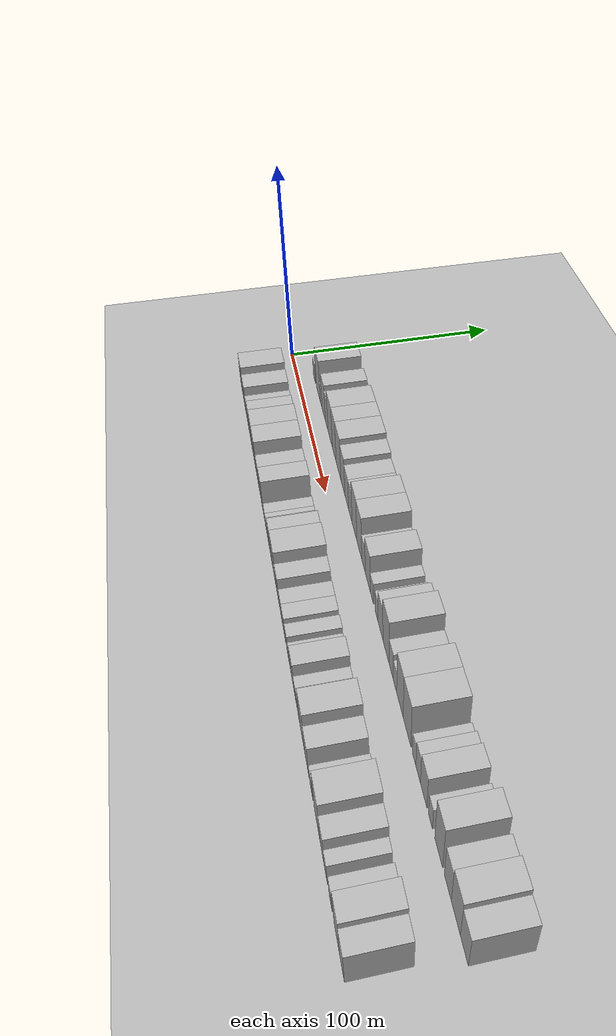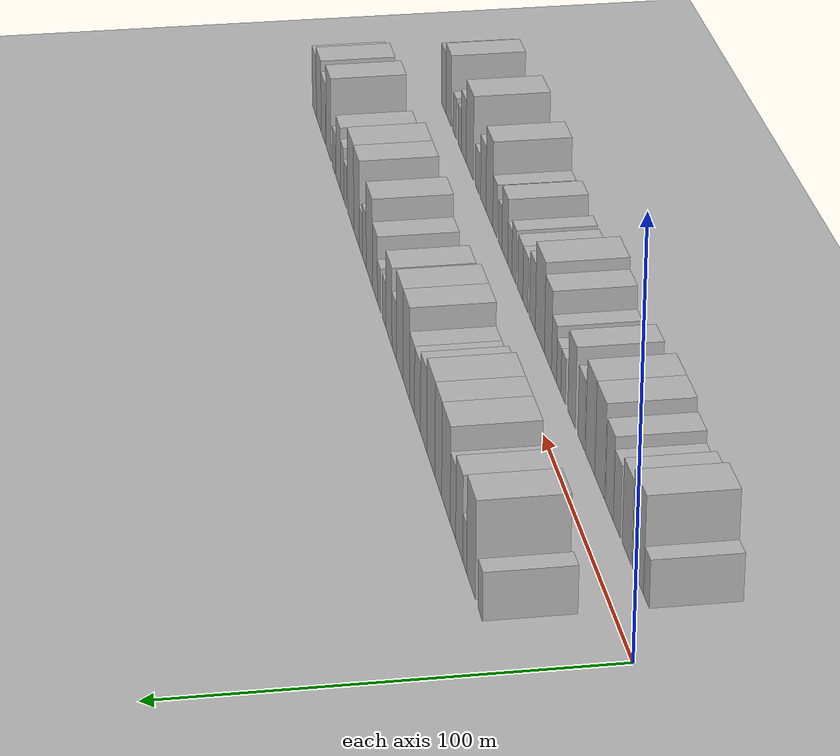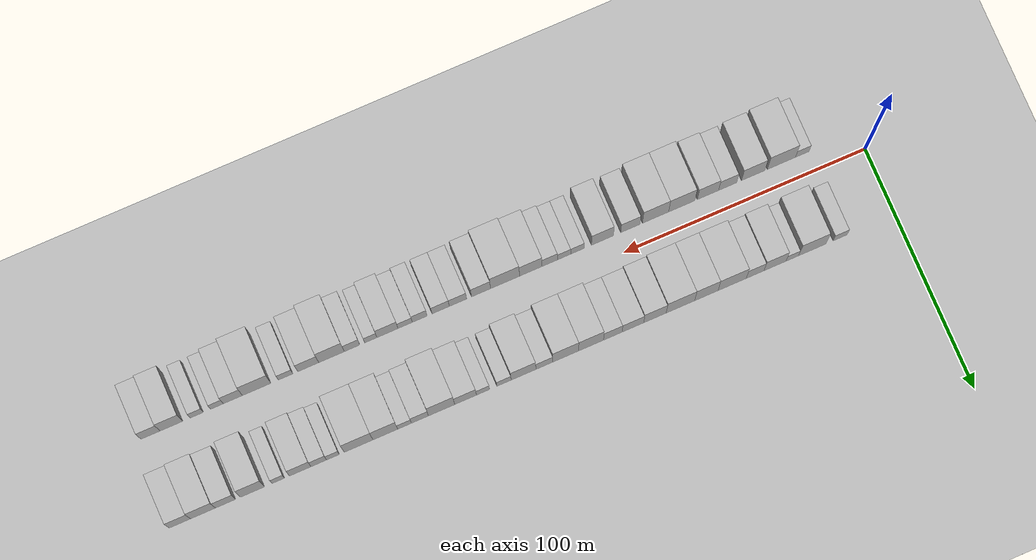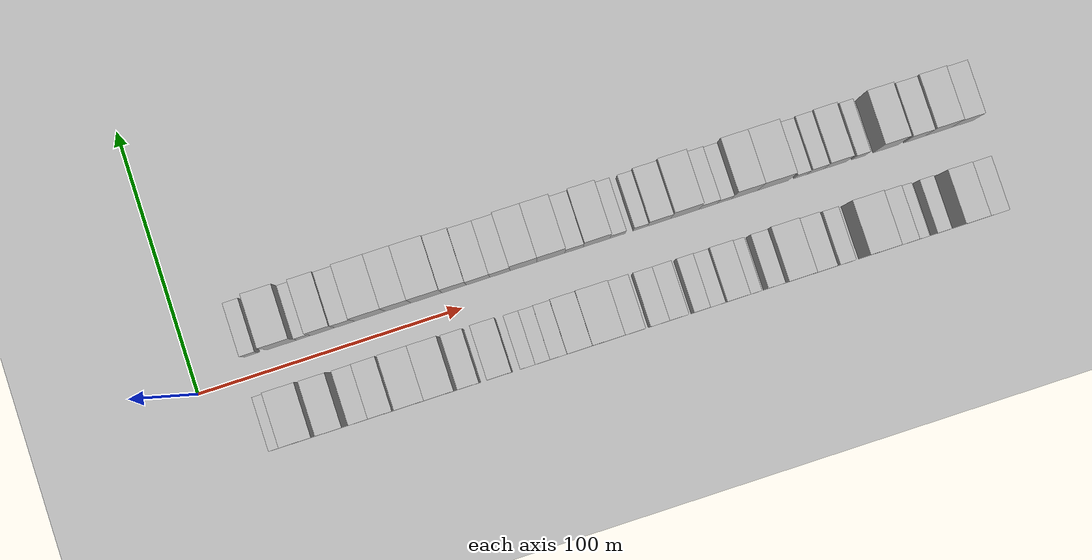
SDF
<?xml version="1.0" encoding="utf-8"?>

<sdf version="1.6">

   <world name="default">

      <gui fullscreen="0">

         <camera name="user_camera">

            <pose>-15 0 4.57585 0 0 0</pose>

            <view_controller>orbit</view_controller>

         </camera>

      </gui>

      <scene>

         <sky>

           <clouds>

             <speed>12</speed>

           </clouds>

         </sky>

         <ambient>0.4 0.4 0.4 1</ambient>

         <background>0.7 0.7 0.7 1</background>

         <shadows>1</shadows>

      </scene>

      <gravity>0 0 -9.8066</gravity>

      <magnetic_field>6e-06 2.3e-05 -4.2e-05</magnetic_field>

      <physics default="0" name="default_physics" type="ode">

         <ode>

            <solver>

               <type>quick</type>

               <iters>10</iters>

               <sor>1.0</sor>

               <use_dynamic_moi_rescaling>0</use_dynamic_moi_rescaling>

            </solver>

            <constraints>

               <cfm>0</cfm>

               <erp>0.2</erp>

               <contact_max_correcting_vel>100</contact_max_correcting_vel>

               <contact_surface_layer>0.001</contact_surface_layer>

            </constraints>

         </ode>

         <max_step_size>0.004</max_step_size>

         <real_time_factor>1</real_time_factor>

         <real_time_update_rate>250</real_time_update_rate>

      </physics>

      <light name="sun" type="directional">

         <cast_shadows>1</cast_shadows>

         <pose>0 0 10 0 0 0</pose>

         <diffuse>0.8 0.8 0.8 1</diffuse>

         <specular>0.2 0.2 0.2 1</specular>

         <attenuation>

            <range>1000</range>

            <constant>0.9</constant>

            <linear>0.01</linear>

            <quadratic>0.001</quadratic>

         </attenuation>

         <direction>-0.5 0.1 -0.9</direction>

      </light>

      <include>

         <name>ground_plane_1</name>

         <uri>model://HANNAS_ground_plane</uri>

         <pose>0 0 0  0 0 0</pose>

      </include>

      <include>

         <name>ground_plane_2</name>

         <uri>model://HANNAS_ground_plane</uri>

         <pose>100 0 0  0 0 0</pose>

      </include>

      <model name="building_1">

         <static>1</static>

         <pose frame="">22.8882 17.5000 0 0.000000 0.000000 1.570796</pose>

         <link name="link">

            <pose frame="">0 0 6.00 0 0 0</pose>

            <collision name="collision">

               <geometry>

                  <box>

                     <size>20.0000 5.7763 12.0000</size>

                  </box>

               </geometry>

               <max_contacts>10</max_contacts>

               <surface>

                  <contact>

                     <ode/>

                  </contact>

                  <bounce/>

                  <friction>

                     <torsional>

                        <ode/>

                     </torsional>

                     <ode/>

                  </friction>

               </surface>

            </collision>

            <visual name="visual">

               <cast_shadows>0</cast_shadows>

               <geometry>

                  <box>

                     <size>20.0000 5.7763 12.0000</size>

                  </box>

               </geometry>

               <material>

                  <script>

                     <uri>model://HANNAS_wall/materials/scripts</uri>

                     <uri>model://HANNAS_wall/materials/textures</uri>

                     <name>vrc/HANNAS_wall</name>

                  </script>

               </material>

            </visual>

            <self_collide>0</self_collide>

            <enable_wind>0</enable_wind>

            <kinematic>0</kinematic>

         </link>

      </model>

      <model name="building_2">

         <static>1</static>

         <pose frame="">34.4393 17.5000 0 0.000000 0.000000 1.570796</pose>

         <link name="link">

            <pose frame="">0 0 12.00 0 0 0</pose>

            <collision name="collision">

               <geometry>

                  <box>

                     <size>20.0000 11.3260 24.0000</size>

                  </box>

               </geometry>

               <max_contacts>10</max_contacts>

               <surface>

                  <contact>

                     <ode/>

                  </contact>

                  <bounce/>

                  <friction>

                     <torsional>

                        <ode/>

                     </torsional>

                     <ode/>

                  </friction>

               </surface>

            </collision>

            <visual name="visual">

               <cast_shadows>0</cast_shadows>

               <geometry>

                  <box>

                     <size>20.0000 11.3260 24.0000</size>

                  </box>

               </geometry>

               <material>

                  <script>

                     <uri>model://HANNAS_wall/materials/scripts</uri>

                     <uri>model://HANNAS_wall/materials/textures</uri>

                     <name>vrc/HANNAS_wall</name>

                  </script>

               </material>

            </visual>

            <self_collide>0</self_collide>

            <enable_wind>0</enable_wind>

            <kinematic>0</kinematic>

         </link>

      </model>

      <model name="building_3">

         <static>1</static>

         <pose frame="">42.7061 17.5000 0 0.000000 0.000000 1.570796</pose>

         <link name="link">

            <pose frame="">0 0 6.00 0 0 0</pose>

            <collision name="collision">

               <geometry>

                  <box>

                     <size>20.0000 5.2077 12.0000</size>

                  </box>

               </geometry>

               <max_contacts>10</max_contacts>

               <surface>

                  <contact>

                     <ode/>

                  </contact>

                  <bounce/>

                  <friction>

                     <torsional>

                        <ode/>

                     </torsional>

                     <ode/>

                  </friction>

               </surface>

            </collision>

            <visual name="visual">

               <cast_shadows>0</cast_shadows>

               <geometry>

                  <box>

                     <size>20.0000 5.2077 12.0000</size>

                  </box>

               </geometry>

               <material>

                  <script>

                     <uri>model://HANNAS_wall/materials/scripts</uri>

                     <uri>model://HANNAS_wall/materials/textures</uri>

                     <name>vrc/HANNAS_wall</name>

                  </script>

               </material>

            </visual>

            <self_collide>0</self_collide>

            <enable_wind>0</enable_wind>

            <kinematic>0</kinematic>

         </link>

      </model>

      <model name="building_4">

         <static>1</static>

         <pose frame="">49.8736 17.5000 0 0.000000 0.000000 1.570796</pose>

         <link name="link">

            <pose frame="">0 0 10.50 0 0 0</pose>

            <collision name="collision">

               <geometry>

                  <box>

                     <size>20.0000 9.1274 21.0000</size>

                  </box>

               </geometry>

               <max_contacts>10</max_contacts>

               <surface>

                  <contact>

                     <ode/>

                  </contact>

                  <bounce/>

                  <friction>

                     <torsional>

                        <ode/>

                     </torsional>

                     <ode/>

                  </friction>

               </surface>

            </collision>

            <visual name="visual">

               <cast_shadows>0</cast_shadows>

               <geometry>

                  <box>

                     <size>20.0000 9.1274 21.0000</size>

                  </box>

               </geometry>

               <material>

                  <script>

                     <uri>model://HANNAS_wall/materials/scripts</uri>

                     <uri>model://HANNAS_wall/materials/textures</uri>

                     <name>vrc/HANNAS_wall</name>

                  </script>

               </material>

            </visual>

            <self_collide>0</self_collide>

            <enable_wind>0</enable_wind>

            <kinematic>0</kinematic>

         </link>

      </model>

      <model name="building_5">

         <static>1</static>

         <pose frame="">58.1065 17.5000 0 0.000000 0.000000 1.570796</pose>

         <link name="link">

            <pose frame="">0 0 9.00 0 0 0</pose>

            <collision name="collision">

               <geometry>

                  <box>

                     <size>20.0000 7.3383 18.0000</size>

                  </box>

               </geometry>

               <max_contacts>10</max_contacts>

               <surface>

                  <contact>

                     <ode/>

                  </contact>

                  <bounce/>

                  <friction>

                     <torsional>

                        <ode/>

                     </torsional>

                     <ode/>

                  </friction>

               </surface>

            </collision>

            <visual name="visual">

               <cast_shadows>0</cast_shadows>

               <geometry>

                  <box>

                     <size>20.0000 7.3383 18.0000</size>

                  </box>

               </geometry>

               <material>

                  <script>

                     <uri>model://HANNAS_wall/materials/scripts</uri>

                     <uri>model://HANNAS_wall/materials/textures</uri>

                     <name>vrc/HANNAS_wall</name>

                  </script>

               </material>

            </visual>

            <self_collide>0</self_collide>

            <enable_wind>0</enable_wind>

            <kinematic>0</kinematic>

         </link>

      </model>

      <model name="building_6">

         <static>1</static>

         <pose frame="">67.6058 17.5000 0 0.000000 0.000000 1.570796</pose>

         <link name="link">

            <pose frame="">0 0 12.00 0 0 0</pose>

            <collision name="collision">

               <geometry>

                  <box>

                     <size>20.0000 11.6603 24.0000</size>

                  </box>

               </geometry>

               <max_contacts>10</max_contacts>

               <surface>

                  <contact>

                     <ode/>

                  </contact>

                  <bounce/>

                  <friction>

                     <torsional>

                        <ode/>

                     </torsional>

                     <ode/>

                  </friction>

               </surface>

            </collision>

            <visual name="visual">

               <cast_shadows>0</cast_shadows>

               <geometry>

                  <box>

                     <size>20.0000 11.6603 24.0000</size>

                  </box>

               </geometry>

               <material>

                  <script>

                     <uri>model://HANNAS_wall/materials/scripts</uri>

                     <uri>model://HANNAS_wall/materials/textures</uri>

                     <name>vrc/HANNAS_wall</name>

                  </script>

               </material>

            </visual>

            <self_collide>0</self_collide>

            <enable_wind>0</enable_wind>

            <kinematic>0</kinematic>

         </link>

      </model>

      <model name="building_7">

         <static>1</static>

         <pose frame="">78.2580 17.5000 0 0.000000 0.000000 1.570796</pose>

         <link name="link">

            <pose frame="">0 0 12.00 0 0 0</pose>

            <collision name="collision">

               <geometry>

                  <box>

                     <size>20.0000 9.6441 24.0000</size>

                  </box>

               </geometry>

               <max_contacts>10</max_contacts>

               <surface>

                  <contact>

                     <ode/>

                  </contact>

                  <bounce/>

                  <friction>

                     <torsional>

                        <ode/>

                     </torsional>

                     <ode/>

                  </friction>

               </surface>

            </collision>

            <visual name="visual">

               <cast_shadows>0</cast_shadows>

               <geometry>

                  <box>

                     <size>20.0000 9.6441 24.0000</size>

                  </box>

               </geometry>

               <material>

                  <script>

                     <uri>model://HANNAS_wall/materials/scripts</uri>

                     <uri>model://HANNAS_wall/materials/textures</uri>

                     <name>vrc/HANNAS_wall</name>

                  </script>

               </material>

            </visual>

            <self_collide>0</self_collide>

            <enable_wind>0</enable_wind>

            <kinematic>0</kinematic>

         </link>

      </model>

      <model name="building_8">

         <static>1</static>

         <pose frame="">88.9379 17.5000 0 0.000000 0.000000 1.570796</pose>

         <link name="link">

            <pose frame="">0 0 12.00 0 0 0</pose>

            <collision name="collision">

               <geometry>

                  <box>

                     <size>20.0000 11.7156 24.0000</size>

                  </box>

               </geometry>

               <max_contacts>10</max_contacts>

               <surface>

                  <contact>

                     <ode/>

                  </contact>

                  <bounce/>

                  <friction>

                     <torsional>

                        <ode/>

                     </torsional>

                     <ode/>

                  </friction>

               </surface>

            </collision>

            <visual name="visual">

               <cast_shadows>0</cast_shadows>

               <geometry>

                  <box>

                     <size>20.0000 11.7156 24.0000</size>

                  </box>

               </geometry>

               <material>

                  <script>

                     <uri>model://HANNAS_wall/materials/scripts</uri>

                     <uri>model://HANNAS_wall/materials/textures</uri>

                     <name>vrc/HANNAS_wall</name>

                  </script>

               </material>

            </visual>

            <self_collide>0</self_collide>

            <enable_wind>0</enable_wind>

            <kinematic>0</kinematic>

         </link>

      </model>

      <model name="building_9">

         <static>1</static>

         <pose frame="">99.4407 17.5000 0 0.000000 0.000000 1.570796</pose>

         <link name="link">

            <pose frame="">0 0 10.50 0 0 0</pose>

            <collision name="collision">

               <geometry>

                  <box>

                     <size>20.0000 9.2900 21.0000</size>

                  </box>

               </geometry>

               <max_contacts>10</max_contacts>

               <surface>

                  <contact>

                     <ode/>

                  </contact>

                  <bounce/>

                  <friction>

                     <torsional>

                        <ode/>

                     </torsional>

                     <ode/>

                  </friction>

               </surface>

            </collision>

            <visual name="visual">

               <cast_shadows>0</cast_shadows>

               <geometry>

                  <box>

                     <size>20.0000 9.2900 21.0000</size>

                  </box>

               </geometry>

               <material>

                  <script>

                     <uri>model://HANNAS_wall/materials/scripts</uri>

                     <uri>model://HANNAS_wall/materials/textures</uri>

                     <name>vrc/HANNAS_wall</name>

                  </script>

               </material>

            </visual>

            <self_collide>0</self_collide>

            <enable_wind>0</enable_wind>

            <kinematic>0</kinematic>

         </link>

      </model>

      <model name="building_10">

         <static>1</static>

         <pose frame="">108.5263 17.5000 0 0.000000 0.000000 1.570796</pose>

         <link name="link">

            <pose frame="">0 0 9.00 0 0 0</pose>

            <collision name="collision">

               <geometry>

                  <box>

                     <size>20.0000 8.8813 18.0000</size>

                  </box>

               </geometry>

               <max_contacts>10</max_contacts>

               <surface>

                  <contact>

                     <ode/>

                  </contact>

                  <bounce/>

                  <friction>

                     <torsional>

                        <ode/>

                     </torsional>

                     <ode/>

                  </friction>

               </surface>

            </collision>

            <visual name="visual">

               <cast_shadows>0</cast_shadows>

               <geometry>

                  <box>

                     <size>20.0000 8.8813 18.0000</size>

                  </box>

               </geometry>

               <material>

                  <script>

                     <uri>model://HANNAS_wall/materials/scripts</uri>

                     <uri>model://HANNAS_wall/materials/textures</uri>

                     <name>vrc/HANNAS_wall</name>

                  </script>

               </material>

            </visual>

            <self_collide>0</self_collide>

            <enable_wind>0</enable_wind>

            <kinematic>0</kinematic>

         </link>

      </model>

      <model name="building_11">

         <static>1</static>

         <pose frame="">116.7841 17.5000 0 0.000000 0.000000 1.570796</pose>

         <link name="link">

            <pose frame="">0 0 9.00 0 0 0</pose>

            <collision name="collision">

               <geometry>

                  <box>

                     <size>20.0000 7.6343 18.0000</size>

                  </box>

               </geometry>

               <max_contacts>10</max_contacts>

               <surface>

                  <contact>

                     <ode/>

                  </contact>

                  <bounce/>

                  <friction>

                     <torsional>

                        <ode/>

                     </torsional>

                     <ode/>

                  </friction>

               </surface>

            </collision>

            <visual name="visual">

               <cast_shadows>0</cast_shadows>

               <geometry>

                  <box>

                     <size>20.0000 7.6343 18.0000</size>

                  </box>

               </geometry>

               <material>

                  <script>

                     <uri>model://HANNAS_wall/materials/scripts</uri>

                     <uri>model://HANNAS_wall/materials/textures</uri>

                     <name>vrc/HANNAS_wall</name>

                  </script>

               </material>

            </visual>

            <self_collide>0</self_collide>

            <enable_wind>0</enable_wind>

            <kinematic>0</kinematic>

         </link>

      </model>

      <model name="building_12">

         <static>1</static>

         <pose frame="">125.7066 17.5000 0 0.000000 0.000000 1.570796</pose>

         <link name="link">

            <pose frame="">0 0 12.00 0 0 0</pose>

            <collision name="collision">

               <geometry>

                  <box>

                     <size>20.0000 10.2106 24.0000</size>

                  </box>

               </geometry>

               <max_contacts>10</max_contacts>

               <surface>

                  <contact>

                     <ode/>

                  </contact>

                  <bounce/>

                  <friction>

                     <torsional>

                        <ode/>

                     </torsional>

                     <ode/>

                  </friction>

               </surface>

            </collision>

            <visual name="visual">

               <cast_shadows>0</cast_shadows>

               <geometry>

                  <box>

                     <size>20.0000 10.2106 24.0000</size>

                  </box>

               </geometry>

               <material>

                  <script>

                     <uri>model://HANNAS_wall/materials/scripts</uri>

                     <uri>model://HANNAS_wall/materials/textures</uri>

                     <name>vrc/HANNAS_wall</name>

                  </script>

               </material>

            </visual>

            <self_collide>0</self_collide>

            <enable_wind>0</enable_wind>

            <kinematic>0</kinematic>

         </link>

      </model>

      <model name="building_13">

         <static>1</static>

         <pose frame="">136.1123 17.5000 0 0.000000 0.000000 1.570796</pose>

         <link name="link">

            <pose frame="">0 0 12.00 0 0 0</pose>

            <collision name="collision">

               <geometry>

                  <box>

                     <size>20.0000 10.6009 24.0000</size>

                  </box>

               </geometry>

               <max_contacts>10</max_contacts>

               <surface>

                  <contact>

                     <ode/>

                  </contact>

                  <bounce/>

                  <friction>

                     <torsional>

                        <ode/>

                     </torsional>

                     <ode/>

                  </friction>

               </surface>

            </collision>

            <visual name="visual">

               <cast_shadows>0</cast_shadows>

               <geometry>

                  <box>

                     <size>20.0000 10.6009 24.0000</size>

                  </box>

               </geometry>

               <material>

                  <script>

                     <uri>model://HANNAS_wall/materials/scripts</uri>

                     <uri>model://HANNAS_wall/materials/textures</uri>

                     <name>vrc/HANNAS_wall</name>

                  </script>

               </material>

            </visual>

            <self_collide>0</self_collide>

            <enable_wind>0</enable_wind>

            <kinematic>0</kinematic>

         </link>

      </model>

      <model name="building_14">

         <static>1</static>

         <pose frame="">144.8784 17.5000 0 0.000000 0.000000 1.570796</pose>

         <link name="link">

            <pose frame="">0 0 7.50 0 0 0</pose>

            <collision name="collision">

               <geometry>

                  <box>

                     <size>20.0000 6.9312 15.0000</size>

                  </box>

               </geometry>

               <max_contacts>10</max_contacts>

               <surface>

                  <contact>

                     <ode/>

                  </contact>

                  <bounce/>

                  <friction>

                     <torsional>

                        <ode/>

                     </torsional>

                     <ode/>

                  </friction>

               </surface>

            </collision>

            <visual name="visual">

               <cast_shadows>0</cast_shadows>

               <geometry>

                  <box>

                     <size>20.0000 6.9312 15.0000</size>

                  </box>

               </geometry>

               <material>

                  <script>

                     <uri>model://HANNAS_wall/materials/scripts</uri>

                     <uri>model://HANNAS_wall/materials/textures</uri>

                     <name>vrc/HANNAS_wall</name>

                  </script>

               </material>

            </visual>

            <self_collide>0</self_collide>

            <enable_wind>0</enable_wind>

            <kinematic>0</kinematic>

         </link>

      </model>

      <model name="building_15">

         <static>1</static>

         <pose frame="">153.4065 17.5000 0 0.000000 0.000000 1.570796</pose>

         <link name="link">

            <pose frame="">0 0 10.50 0 0 0</pose>

            <collision name="collision">

               <geometry>

                  <box>

                     <size>20.0000 10.1251 21.0000</size>

                  </box>

               </geometry>

               <max_contacts>10</max_contacts>

               <surface>

                  <contact>

                     <ode/>

                  </contact>

                  <bounce/>

                  <friction>

                     <torsional>

                        <ode/>

                     </torsional>

                     <ode/>

                  </friction>

               </surface>

            </collision>

            <visual name="visual">

               <cast_shadows>0</cast_shadows>

               <geometry>

                  <box>

                     <size>20.0000 10.1251 21.0000</size>

                  </box>

               </geometry>

               <material>

                  <script>

                     <uri>model://HANNAS_wall/materials/scripts</uri>

                     <uri>model://HANNAS_wall/materials/textures</uri>

                     <name>vrc/HANNAS_wall</name>

                  </script>

               </material>

            </visual>

            <self_collide>0</self_collide>

            <enable_wind>0</enable_wind>

            <kinematic>0</kinematic>

         </link>

      </model>

      <model name="building_16">

         <static>1</static>

         <pose frame="">161.3831 17.5000 0 0.000000 0.000000 1.570796</pose>

         <link name="link">

            <pose frame="">0 0 6.00 0 0 0</pose>

            <collision name="collision">

               <geometry>

                  <box>

                     <size>20.0000 5.8283 12.0000</size>

                  </box>

               </geometry>

               <max_contacts>10</max_contacts>

               <surface>

                  <contact>

                     <ode/>

                  </contact>

                  <bounce/>

                  <friction>

                     <torsional>

                        <ode/>

                     </torsional>

                     <ode/>

                  </friction>

               </surface>

            </collision>

            <visual name="visual">

               <cast_shadows>0</cast_shadows>

               <geometry>

                  <box>

                     <size>20.0000 5.8283 12.0000</size>

                  </box>

               </geometry>

               <material>

                  <script>

                     <uri>model://HANNAS_wall/materials/scripts</uri>

                     <uri>model://HANNAS_wall/materials/textures</uri>

                     <name>vrc/HANNAS_wall</name>

                  </script>

               </material>

            </visual>

            <self_collide>0</self_collide>

            <enable_wind>0</enable_wind>

            <kinematic>0</kinematic>

         </link>

      </model>

      <model name="building_17">

         <static>1</static>

         <pose frame="">169.9986 17.5000 0 0.000000 0.000000 1.570796</pose>

         <link name="link">

            <pose frame="">0 0 6.00 0 0 0</pose>

            <collision name="collision">

               <geometry>

                  <box>

                     <size>20.0000 5.4027 12.0000</size>

                  </box>

               </geometry>

               <max_contacts>10</max_contacts>

               <surface>

                  <contact>

                     <ode/>

                  </contact>

                  <bounce/>

                  <friction>

                     <torsional>

                        <ode/>

                     </torsional>

                     <ode/>

                  </friction>

               </surface>

            </collision>

            <visual name="visual">

               <cast_shadows>0</cast_shadows>

               <geometry>

                  <box>

                     <size>20.0000 5.4027 12.0000</size>

                  </box>

               </geometry>

               <material>

                  <script>

                     <uri>model://HANNAS_wall/materials/scripts</uri>

                     <uri>model://HANNAS_wall/materials/textures</uri>

                     <name>vrc/HANNAS_wall</name>

                  </script>

               </material>

            </visual>

            <self_collide>0</self_collide>

            <enable_wind>0</enable_wind>

            <kinematic>0</kinematic>

         </link>

      </model>

      <model name="building_18">

         <static>1</static>

         <pose frame="">177.1372 17.5000 0 0.000000 0.000000 1.570796</pose>

         <link name="link">

            <pose frame="">0 0 9.00 0 0 0</pose>

            <collision name="collision">

               <geometry>

                  <box>

                     <size>20.0000 8.8744 18.0000</size>

                  </box>

               </geometry>

               <max_contacts>10</max_contacts>

               <surface>

                  <contact>

                     <ode/>

                  </contact>

                  <bounce/>

                  <friction>

                     <torsional>

                        <ode/>

                     </torsional>

                     <ode/>

                  </friction>

               </surface>

            </collision>

            <visual name="visual">

               <cast_shadows>0</cast_shadows>

               <geometry>

                  <box>

                     <size>20.0000 8.8744 18.0000</size>

                  </box>

               </geometry>

               <material>

                  <script>

                     <uri>model://HANNAS_wall/materials/scripts</uri>

                     <uri>model://HANNAS_wall/materials/textures</uri>

                     <name>vrc/HANNAS_wall</name>

                  </script>

               </material>

            </visual>

            <self_collide>0</self_collide>

            <enable_wind>0</enable_wind>

            <kinematic>0</kinematic>

         </link>

      </model>

      <model name="building_19">

         <static>1</static>

         <pose frame="">186.9321 17.5000 0 0.000000 0.000000 1.570796</pose>

         <link name="link">

            <pose frame="">0 0 12.00 0 0 0</pose>

            <collision name="collision">

               <geometry>

                  <box>

                     <size>20.0000 10.7153 24.0000</size>

                  </box>

               </geometry>

               <max_contacts>10</max_contacts>

               <surface>

                  <contact>

                     <ode/>

                  </contact>

                  <bounce/>

                  <friction>

                     <torsional>

                        <ode/>

                     </torsional>

                     <ode/>

                  </friction>

               </surface>

            </collision>

            <visual name="visual">

               <cast_shadows>0</cast_shadows>

               <geometry>

                  <box>

                     <size>20.0000 10.7153 24.0000</size>

                  </box>

               </geometry>

               <material>

                  <script>

                     <uri>model://HANNAS_wall/materials/scripts</uri>

                     <uri>model://HANNAS_wall/materials/textures</uri>

                     <name>vrc/HANNAS_wall</name>

                  </script>

               </material>

            </visual>

            <self_collide>0</self_collide>

            <enable_wind>0</enable_wind>

            <kinematic>0</kinematic>

         </link>

      </model>

      <model name="building_20">

         <static>1</static>

         <pose frame="">195.7815 17.5000 0 0.000000 0.000000 1.570796</pose>

         <link name="link">

            <pose frame="">0 0 7.50 0 0 0</pose>

            <collision name="collision">

               <geometry>

                  <box>

                     <size>20.0000 6.9834 15.0000</size>

                  </box>

               </geometry>

               <max_contacts>10</max_contacts>

               <surface>

                  <contact>

                     <ode/>

                  </contact>

                  <bounce/>

                  <friction>

                     <torsional>

                        <ode/>

                     </torsional>

                     <ode/>

                  </friction>

               </surface>

            </collision>

            <visual name="visual">

               <cast_shadows>0</cast_shadows>

               <geometry>

                  <box>

                     <size>20.0000 6.9834 15.0000</size>

                  </box>

               </geometry>

               <material>

                  <script>

                     <uri>model://HANNAS_wall/materials/scripts</uri>

                     <uri>model://HANNAS_wall/materials/textures</uri>

                     <name>vrc/HANNAS_wall</name>

                  </script>

               </material>

            </visual>

            <self_collide>0</self_collide>

            <enable_wind>0</enable_wind>

            <kinematic>0</kinematic>

         </link>

      </model>

      <model name="building_21">

         <static>1</static>

         <pose frame="">202.0707 17.5000 0 0.000000 0.000000 1.570796</pose>

         <link name="link">

            <pose frame="">0 0 6.00 0 0 0</pose>

            <collision name="collision">

               <geometry>

                  <box>

                     <size>20.0000 5.5950 12.0000</size>

                  </box>

               </geometry>

               <max_contacts>10</max_contacts>

               <surface>

                  <contact>

                     <ode/>

                  </contact>

                  <bounce/>

                  <friction>

                     <torsional>

                        <ode/>

                     </torsional>

                     <ode/>

                  </friction>

               </surface>

            </collision>

            <visual name="visual">

               <cast_shadows>0</cast_shadows>

               <geometry>

                  <box>

                     <size>20.0000 5.5950 12.0000</size>

                  </box>

               </geometry>

               <material>

                  <script>

                     <uri>model://HANNAS_wall/materials/scripts</uri>

                     <uri>model://HANNAS_wall/materials/textures</uri>

                     <name>vrc/HANNAS_wall</name>

                  </script>

               </material>

            </visual>

            <self_collide>0</self_collide>

            <enable_wind>0</enable_wind>

            <kinematic>0</kinematic>

         </link>

      </model>

      <model name="building_22">

         <static>1</static>

         <pose frame="">209.8988 17.5000 0 0.000000 0.000000 1.570796</pose>

         <link name="link">

            <pose frame="">0 0 12.00 0 0 0</pose>

            <collision name="collision">

               <geometry>

                  <box>

                     <size>20.0000 10.0612 24.0000</size>

                  </box>

               </geometry>

               <max_contacts>10</max_contacts>

               <surface>

                  <contact>

                     <ode/>

                  </contact>

                  <bounce/>

                  <friction>

                     <torsional>

                        <ode/>

                     </torsional>

                     <ode/>

                  </friction>

               </surface>

            </collision>

            <visual name="visual">

               <cast_shadows>0</cast_shadows>

               <geometry>

                  <box>

                     <size>20.0000 10.0612 24.0000</size>

                  </box>

               </geometry>

               <material>

                  <script>

                     <uri>model://HANNAS_wall/materials/scripts</uri>

                     <uri>model://HANNAS_wall/materials/textures</uri>

                     <name>vrc/HANNAS_wall</name>

                  </script>

               </material>

            </visual>

            <self_collide>0</self_collide>

            <enable_wind>0</enable_wind>

            <kinematic>0</kinematic>

         </link>

      </model>

      <model name="building_23">

         <static>1</static>

         <pose frame="">220.7700 17.5000 0 0.000000 0.000000 1.570796</pose>

         <link name="link">

            <pose frame="">0 0 12.00 0 0 0</pose>

            <collision name="collision">

               <geometry>

                  <box>

                     <size>20.0000 11.6812 24.0000</size>

                  </box>

               </geometry>

               <max_contacts>10</max_contacts>

               <surface>

                  <contact>

                     <ode/>

                  </contact>

                  <bounce/>

                  <friction>

                     <torsional>

                        <ode/>

                     </torsional>

                     <ode/>

                  </friction>

               </surface>

            </collision>

            <visual name="visual">

               <cast_shadows>0</cast_shadows>

               <geometry>

                  <box>

                     <size>20.0000 11.6812 24.0000</size>

                  </box>

               </geometry>

               <material>

                  <script>

                     <uri>model://HANNAS_wall/materials/scripts</uri>

                     <uri>model://HANNAS_wall/materials/textures</uri>

                     <name>vrc/HANNAS_wall</name>

                  </script>

               </material>

            </visual>

            <self_collide>0</self_collide>

            <enable_wind>0</enable_wind>

            <kinematic>0</kinematic>

         </link>

      </model>

      <model name="building_24">

         <static>1</static>

         <pose frame="">231.2007 17.5000 0 0.000000 0.000000 1.570796</pose>

         <link name="link">

            <pose frame="">0 0 6.00 0 0 0</pose>

            <collision name="collision">

               <geometry>

                  <box>

                     <size>20.0000 5.1802 12.0000</size>

                  </box>

               </geometry>

               <max_contacts>10</max_contacts>

               <surface>

                  <contact>

                     <ode/>

                  </contact>

                  <bounce/>

                  <friction>

                     <torsional>

                        <ode/>

                     </torsional>

                     <ode/>

                  </friction>

               </surface>

            </collision>

            <visual name="visual">

               <cast_shadows>0</cast_shadows>

               <geometry>

                  <box>

                     <size>20.0000 5.1802 12.0000</size>

                  </box>

               </geometry>

               <material>

                  <script>

                     <uri>model://HANNAS_wall/materials/scripts</uri>

                     <uri>model://HANNAS_wall/materials/textures</uri>

                     <name>vrc/HANNAS_wall</name>

                  </script>

               </material>

            </visual>

            <self_collide>0</self_collide>

            <enable_wind>0</enable_wind>

            <kinematic>0</kinematic>

         </link>

      </model>

      <model name="building_25">

         <static>1</static>

         <pose frame="">236.9427 17.5000 0 0.000000 0.000000 1.570796</pose>

         <link name="link">

            <pose frame="">0 0 7.50 0 0 0</pose>

            <collision name="collision">

               <geometry>

                  <box>

                     <size>20.0000 6.3038 15.0000</size>

                  </box>

               </geometry>

               <max_contacts>10</max_contacts>

               <surface>

                  <contact>

                     <ode/>

                  </contact>

                  <bounce/>

                  <friction>

                     <torsional>

                        <ode/>

                     </torsional>

                     <ode/>

                  </friction>

               </surface>

            </collision>

            <visual name="visual">

               <cast_shadows>0</cast_shadows>

               <geometry>

                  <box>

                     <size>20.0000 6.3038 15.0000</size>

                  </box>

               </geometry>

               <material>

                  <script>

                     <uri>model://HANNAS_wall/materials/scripts</uri>

                     <uri>model://HANNAS_wall/materials/textures</uri>

                     <name>vrc/HANNAS_wall</name>

                  </script>

               </material>

            </visual>

            <self_collide>0</self_collide>

            <enable_wind>0</enable_wind>

            <kinematic>0</kinematic>

         </link>

      </model>

      <model name="building_26">

         <static>1</static>

         <pose frame="">244.4711 17.5000 0 0.000000 0.000000 1.570796</pose>

         <link name="link">

            <pose frame="">0 0 9.00 0 0 0</pose>

            <collision name="collision">

               <geometry>

                  <box>

                     <size>20.0000 8.7531 18.0000</size>

                  </box>

               </geometry>

               <max_contacts>10</max_contacts>

               <surface>

                  <contact>

                     <ode/>

                  </contact>

                  <bounce/>

                  <friction>

                     <torsional>

                        <ode/>

                     </torsional>

                     <ode/>

                  </friction>

               </surface>

            </collision>

            <visual name="visual">

               <cast_shadows>0</cast_shadows>

               <geometry>

                  <box>

                     <size>20.0000 8.7531 18.0000</size>

                  </box>

               </geometry>

               <material>

                  <script>

                     <uri>model://HANNAS_wall/materials/scripts</uri>

                     <uri>model://HANNAS_wall/materials/textures</uri>

                     <name>vrc/HANNAS_wall</name>

                  </script>

               </material>

            </visual>

            <self_collide>0</self_collide>

            <enable_wind>0</enable_wind>

            <kinematic>0</kinematic>

         </link>

      </model>

      <model name="building_27">

         <static>1</static>

         <pose frame="">253.4204 17.5000 0 0.000000 0.000000 1.570796</pose>

         <link name="link">

            <pose frame="">0 0 6.00 0 0 0</pose>

            <collision name="collision">

               <geometry>

                  <box>

                     <size>20.0000 5.1455 12.0000</size>

                  </box>

               </geometry>

               <max_contacts>10</max_contacts>

               <surface>

                  <contact>

                     <ode/>

                  </contact>

                  <bounce/>

                  <friction>

                     <torsional>

                        <ode/>

                     </torsional>

                     <ode/>

                  </friction>

               </surface>

            </collision>

            <visual name="visual">

               <cast_shadows>0</cast_shadows>

               <geometry>

                  <box>

                     <size>20.0000 5.1455 12.0000</size>

                  </box>

               </geometry>

               <material>

                  <script>

                     <uri>model://HANNAS_wall/materials/scripts</uri>

                     <uri>model://HANNAS_wall/materials/textures</uri>

                     <name>vrc/HANNAS_wall</name>

                  </script>

               </material>

            </visual>

            <self_collide>0</self_collide>

            <enable_wind>0</enable_wind>

            <kinematic>0</kinematic>

         </link>

      </model>

      <model name="building_28">

         <static>1</static>

         <pose frame="">263.8647 17.5000 0 0.000000 0.000000 1.570796</pose>

         <link name="link">

            <pose frame="">0 0 12.00 0 0 0</pose>

            <collision name="collision">

               <geometry>

                  <box>

                     <size>20.0000 9.7432 24.0000</size>

                  </box>

               </geometry>

               <max_contacts>10</max_contacts>

               <surface>

                  <contact>

                     <ode/>

                  </contact>

                  <bounce/>

                  <friction>

                     <torsional>

                        <ode/>

                     </torsional>

                     <ode/>

                  </friction>

               </surface>

            </collision>

            <visual name="visual">

               <cast_shadows>0</cast_shadows>

               <geometry>

                  <box>

                     <size>20.0000 9.7432 24.0000</size>

                  </box>

               </geometry>

               <material>

                  <script>

                     <uri>model://HANNAS_wall/materials/scripts</uri>

                     <uri>model://HANNAS_wall/materials/textures</uri>

                     <name>vrc/HANNAS_wall</name>

                  </script>

               </material>

            </visual>

            <self_collide>0</self_collide>

            <enable_wind>0</enable_wind>

            <kinematic>0</kinematic>

         </link>

      </model>

      <model name="building_29">

         <static>1</static>

         <pose frame="">274.8220 17.5000 0 0.000000 0.000000 1.570796</pose>

         <link name="link">

            <pose frame="">0 0 9.00 0 0 0</pose>

            <collision name="collision">

               <geometry>

                  <box>

                     <size>20.0000 8.1714 18.0000</size>

                  </box>

               </geometry>

               <max_contacts>10</max_contacts>

               <surface>

                  <contact>

                     <ode/>

                  </contact>

                  <bounce/>

                  <friction>

                     <torsional>

                        <ode/>

                     </torsional>

                     <ode/>

                  </friction>

               </surface>

            </collision>

            <visual name="visual">

               <cast_shadows>0</cast_shadows>

               <geometry>

                  <box>

                     <size>20.0000 8.1714 18.0000</size>

                  </box>

               </geometry>

               <material>

                  <script>

                     <uri>model://HANNAS_wall/materials/scripts</uri>

                     <uri>model://HANNAS_wall/materials/textures</uri>

                     <name>vrc/HANNAS_wall</name>

                  </script>

               </material>

            </visual>

            <self_collide>0</self_collide>

            <enable_wind>0</enable_wind>

            <kinematic>0</kinematic>

         </link>

      </model>

      <model name="building_30">

         <static>1</static>

         <pose frame="">283.9643 17.5000 0 0.000000 0.000000 1.570796</pose>

         <link name="link">

            <pose frame="">0 0 10.50 0 0 0</pose>

            <collision name="collision">

               <geometry>

                  <box>

                     <size>20.0000 10.1132 21.0000</size>

                  </box>

               </geometry>

               <max_contacts>10</max_contacts>

               <surface>

                  <contact>

                     <ode/>

                  </contact>

                  <bounce/>

                  <friction>

                     <torsional>

                        <ode/>

                     </torsional>

                     <ode/>

                  </friction>

               </surface>

            </collision>

            <visual name="visual">

               <cast_shadows>0</cast_shadows>

               <geometry>

                  <box>

                     <size>20.0000 10.1132 21.0000</size>

                  </box>

               </geometry>

               <material>

                  <script>

                     <uri>model://HANNAS_wall/materials/scripts</uri>

                     <uri>model://HANNAS_wall/materials/textures</uri>

                     <name>vrc/HANNAS_wall</name>

                  </script>

               </material>

            </visual>

            <self_collide>0</self_collide>

            <enable_wind>0</enable_wind>

            <kinematic>0</kinematic>

         </link>

      </model>

      <model name="building_31">

         <static>1</static>

         <pose frame="">293.3305 17.5000 0 0.000000 0.000000 1.570796</pose>

         <link name="link">

            <pose frame="">0 0 9.00 0 0 0</pose>

            <collision name="collision">

               <geometry>

                  <box>

                     <size>20.0000 8.6192 18.0000</size>

                  </box>

               </geometry>

               <max_contacts>10</max_contacts>

               <surface>

                  <contact>

                     <ode/>

                  </contact>

                  <bounce/>

                  <friction>

                     <torsional>

                        <ode/>

                     </torsional>

                     <ode/>

                  </friction>

               </surface>

            </collision>

            <visual name="visual">

               <cast_shadows>0</cast_shadows>

               <geometry>

                  <box>

                     <size>20.0000 8.6192 18.0000</size>

                  </box>

               </geometry>

               <material>

                  <script>

                     <uri>model://HANNAS_wall/materials/scripts</uri>

                     <uri>model://HANNAS_wall/materials/textures</uri>

                     <name>vrc/HANNAS_wall</name>

                  </script>

               </material>

            </visual>

            <self_collide>0</self_collide>

            <enable_wind>0</enable_wind>

            <kinematic>0</kinematic>

         </link>

      </model>

      <model name="building_32">

         <static>1</static>

         <pose frame="">22.8510 -17.5000 0 0.000000 0.000000 1.570796</pose>

         <link name="link">

            <pose frame="">0 0 6.00 0 0 0</pose>

            <collision name="collision">

               <geometry>

                  <box>

                     <size>20.0000 5.7019 12.0000</size>

                  </box>

               </geometry>

               <max_contacts>10</max_contacts>

               <surface>

                  <contact>

                     <ode/>

                  </contact>

                  <bounce/>

                  <friction>

                     <torsional>

                        <ode/>

                     </torsional>

                     <ode/>

                  </friction>

               </surface>

            </collision>

            <visual name="visual">

               <cast_shadows>0</cast_shadows>

               <geometry>

                  <box>

                     <size>20.0000 5.7019 12.0000</size>

                  </box>

               </geometry>

               <material>

                  <script>

                     <uri>model://HANNAS_wall/materials/scripts</uri>

                     <uri>model://HANNAS_wall/materials/textures</uri>

                     <name>vrc/HANNAS_wall</name>

                  </script>

               </material>

            </visual>

            <self_collide>0</self_collide>

            <enable_wind>0</enable_wind>

            <kinematic>0</kinematic>

         </link>

      </model>

      <model name="building_33">

         <static>1</static>

         <pose frame="">31.5597 -17.5000 0 0.000000 0.000000 1.570796</pose>

         <link name="link">

            <pose frame="">0 0 12.00 0 0 0</pose>

            <collision name="collision">

               <geometry>

                  <box>

                     <size>20.0000 11.7155 24.0000</size>

                  </box>

               </geometry>

               <max_contacts>10</max_contacts>

               <surface>

                  <contact>

                     <ode/>

                  </contact>

                  <bounce/>

                  <friction>

                     <torsional>

                        <ode/>

                     </torsional>

                     <ode/>

                  </friction>

               </surface>

            </collision>

            <visual name="visual">

               <cast_shadows>0</cast_shadows>

               <geometry>

                  <box>

                     <size>20.0000 11.7155 24.0000</size>

                  </box>

               </geometry>

               <material>

                  <script>

                     <uri>model://HANNAS_wall/materials/scripts</uri>

                     <uri>model://HANNAS_wall/materials/textures</uri>

                     <name>vrc/HANNAS_wall</name>

                  </script>

               </material>

            </visual>

            <self_collide>0</self_collide>

            <enable_wind>0</enable_wind>

            <kinematic>0</kinematic>

         </link>

      </model>

      <model name="building_34">

         <static>1</static>

         <pose frame="">43.2738 -17.5000 0 0.000000 0.000000 1.570796</pose>

         <link name="link">

            <pose frame="">0 0 10.50 0 0 0</pose>

            <collision name="collision">

               <geometry>

                  <box>

                     <size>20.0000 9.7128 21.0000</size>

                  </box>

               </geometry>

               <max_contacts>10</max_contacts>

               <surface>

                  <contact>

                     <ode/>

                  </contact>

                  <bounce/>

                  <friction>

                     <torsional>

                        <ode/>

                     </torsional>

                     <ode/>

                  </friction>

               </surface>

            </collision>

            <visual name="visual">

               <cast_shadows>0</cast_shadows>

               <geometry>

                  <box>

                     <size>20.0000 9.7128 21.0000</size>

                  </box>

               </geometry>

               <material>

                  <script>

                     <uri>model://HANNAS_wall/materials/scripts</uri>

                     <uri>model://HANNAS_wall/materials/textures</uri>

                     <name>vrc/HANNAS_wall</name>

                  </script>

               </material>

            </visual>

            <self_collide>0</self_collide>

            <enable_wind>0</enable_wind>

            <kinematic>0</kinematic>

         </link>

      </model>

      <model name="building_35">

         <static>1</static>

         <pose frame="">53.8877 -17.5000 0 0.000000 0.000000 1.570796</pose>

         <link name="link">

            <pose frame="">0 0 9.00 0 0 0</pose>

            <collision name="collision">

               <geometry>

                  <box>

                     <size>20.0000 7.5148 18.0000</size>

                  </box>

               </geometry>

               <max_contacts>10</max_contacts>

               <surface>

                  <contact>

                     <ode/>

                  </contact>

                  <bounce/>

                  <friction>

                     <torsional>

                        <ode/>

                     </torsional>

                     <ode/>

                  </friction>

               </surface>

            </collision>

            <visual name="visual">

               <cast_shadows>0</cast_shadows>

               <geometry>

                  <box>

                     <size>20.0000 7.5148 18.0000</size>

                  </box>

               </geometry>

               <material>

                  <script>

                     <uri>model://HANNAS_wall/materials/scripts</uri>

                     <uri>model://HANNAS_wall/materials/textures</uri>

                     <name>vrc/HANNAS_wall</name>

                  </script>

               </material>

            </visual>

            <self_collide>0</self_collide>

            <enable_wind>0</enable_wind>

            <kinematic>0</kinematic>

         </link>

      </model>

      <model name="building_36">

         <static>1</static>

         <pose frame="">62.0545 -17.5000 0 0.000000 0.000000 1.570796</pose>

         <link name="link">

            <pose frame="">0 0 10.50 0 0 0</pose>

            <collision name="collision">

               <geometry>

                  <box>

                     <size>20.0000 8.8189 21.0000</size>

                  </box>

               </geometry>

               <max_contacts>10</max_contacts>

               <surface>

                  <contact>

                     <ode/>

                  </contact>

                  <bounce/>

                  <friction>

                     <torsional>

                        <ode/>

                     </torsional>

                     <ode/>

                  </friction>

               </surface>

            </collision>

            <visual name="visual">

               <cast_shadows>0</cast_shadows>

               <geometry>

                  <box>

                     <size>20.0000 8.8189 21.0000</size>

                  </box>

               </geometry>

               <material>

                  <script>

                     <uri>model://HANNAS_wall/materials/scripts</uri>

                     <uri>model://HANNAS_wall/materials/textures</uri>

                     <name>vrc/HANNAS_wall</name>

                  </script>

               </material>

            </visual>

            <self_collide>0</self_collide>

            <enable_wind>0</enable_wind>

            <kinematic>0</kinematic>

         </link>

      </model>

      <model name="building_37">

         <static>1</static>

         <pose frame="">72.8886 -17.5000 0 0.000000 0.000000 1.570796</pose>

         <link name="link">

            <pose frame="">0 0 12.00 0 0 0</pose>

            <collision name="collision">

               <geometry>

                  <box>

                     <size>20.0000 10.8493 24.0000</size>

                  </box>

               </geometry>

               <max_contacts>10</max_contacts>

               <surface>

                  <contact>

                     <ode/>

                  </contact>

                  <bounce/>

                  <friction>

                     <torsional>

                        <ode/>

                     </torsional>

                     <ode/>

                  </friction>

               </surface>

            </collision>

            <visual name="visual">

               <cast_shadows>0</cast_shadows>

               <geometry>

                  <box>

                     <size>20.0000 10.8493 24.0000</size>

                  </box>

               </geometry>

               <material>

                  <script>

                     <uri>model://HANNAS_wall/materials/scripts</uri>

                     <uri>model://HANNAS_wall/materials/textures</uri>

                     <name>vrc/HANNAS_wall</name>

                  </script>

               </material>

            </visual>

            <self_collide>0</self_collide>

            <enable_wind>0</enable_wind>

            <kinematic>0</kinematic>

         </link>

      </model>

      <model name="building_38">

         <static>1</static>

         <pose frame="">83.7426 -17.5000 0 0.000000 0.000000 1.570796</pose>

         <link name="link">

            <pose frame="">0 0 12.00 0 0 0</pose>

            <collision name="collision">

               <geometry>

                  <box>

                     <size>20.0000 10.8588 24.0000</size>

                  </box>

               </geometry>

               <max_contacts>10</max_contacts>

               <surface>

                  <contact>

                     <ode/>

                  </contact>

                  <bounce/>

                  <friction>

                     <torsional>

                        <ode/>

                     </torsional>

                     <ode/>

                  </friction>

               </surface>

            </collision>

            <visual name="visual">

               <cast_shadows>0</cast_shadows>

               <geometry>

                  <box>

                     <size>20.0000 10.8588 24.0000</size>

                  </box>

               </geometry>

               <material>

                  <script>

                     <uri>model://HANNAS_wall/materials/scripts</uri>

                     <uri>model://HANNAS_wall/materials/textures</uri>

                     <name>vrc/HANNAS_wall</name>

                  </script>

               </material>

            </visual>

            <self_collide>0</self_collide>

            <enable_wind>0</enable_wind>

            <kinematic>0</kinematic>

         </link>

      </model>

      <model name="building_39">

         <static>1</static>

         <pose frame="">94.1570 -17.5000 0 0.000000 0.000000 1.570796</pose>

         <link name="link">

            <pose frame="">0 0 9.00 0 0 0</pose>

            <collision name="collision">

               <geometry>

                  <box>

                     <size>20.0000 7.9699 18.0000</size>

                  </box>

               </geometry>

               <max_contacts>10</max_contacts>

               <surface>

                  <contact>

                     <ode/>

                  </contact>

                  <bounce/>

                  <friction>

                     <torsional>

                        <ode/>

                     </torsional>

                     <ode/>

                  </friction>

               </surface>

            </collision>

            <visual name="visual">

               <cast_shadows>0</cast_shadows>

               <geometry>

                  <box>

                     <size>20.0000 7.9699 18.0000</size>

                  </box>

               </geometry>

               <material>

                  <script>

                     <uri>model://HANNAS_wall/materials/scripts</uri>

                     <uri>model://HANNAS_wall/materials/textures</uri>

                     <name>vrc/HANNAS_wall</name>

                  </script>

               </material>

            </visual>

            <self_collide>0</self_collide>

            <enable_wind>0</enable_wind>

            <kinematic>0</kinematic>

         </link>

      </model>

      <model name="building_40">

         <static>1</static>

         <pose frame="">105.6858 -17.5000 0 0.000000 0.000000 1.570796</pose>

         <link name="link">

            <pose frame="">0 0 10.50 0 0 0</pose>

            <collision name="collision">

               <geometry>

                  <box>

                     <size>20.0000 9.0878 21.0000</size>

                  </box>

               </geometry>

               <max_contacts>10</max_contacts>

               <surface>

                  <contact>

                     <ode/>

                  </contact>

                  <bounce/>

                  <friction>

                     <torsional>

                        <ode/>

                     </torsional>

                     <ode/>

                  </friction>

               </surface>

            </collision>

            <visual name="visual">

               <cast_shadows>0</cast_shadows>

               <geometry>

                  <box>

                     <size>20.0000 9.0878 21.0000</size>

                  </box>

               </geometry>

               <material>

                  <script>

                     <uri>model://HANNAS_wall/materials/scripts</uri>

                     <uri>model://HANNAS_wall/materials/textures</uri>

                     <name>vrc/HANNAS_wall</name>

                  </script>

               </material>

            </visual>

            <self_collide>0</self_collide>

            <enable_wind>0</enable_wind>

            <kinematic>0</kinematic>

         </link>

      </model>

      <model name="building_41">

         <static>1</static>

         <pose frame="">116.0129 -17.5000 0 0.000000 0.000000 1.570796</pose>

         <link name="link">

            <pose frame="">0 0 6.00 0 0 0</pose>

            <collision name="collision">

               <geometry>

                  <box>

                     <size>20.0000 5.5663 12.0000</size>

                  </box>

               </geometry>

               <max_contacts>10</max_contacts>

               <surface>

                  <contact>

                     <ode/>

                  </contact>

                  <bounce/>

                  <friction>

                     <torsional>

                        <ode/>

                     </torsional>

                     <ode/>

                  </friction>

               </surface>

            </collision>

            <visual name="visual">

               <cast_shadows>0</cast_shadows>

               <geometry>

                  <box>

                     <size>20.0000 5.5663 12.0000</size>

                  </box>

               </geometry>

               <material>

                  <script>

                     <uri>model://HANNAS_wall/materials/scripts</uri>

                     <uri>model://HANNAS_wall/materials/textures</uri>

                     <name>vrc/HANNAS_wall</name>

                  </script>

               </material>

            </visual>

            <self_collide>0</self_collide>

            <enable_wind>0</enable_wind>

            <kinematic>0</kinematic>

         </link>

      </model>

      <model name="building_42">

         <static>1</static>

         <pose frame="">121.5412 -17.5000 0 0.000000 0.000000 1.570796</pose>

         <link name="link">

            <pose frame="">0 0 6.00 0 0 0</pose>

            <collision name="collision">

               <geometry>

                  <box>

                     <size>20.0000 5.4905 12.0000</size>

                  </box>

               </geometry>

               <max_contacts>10</max_contacts>

               <surface>

                  <contact>

                     <ode/>

                  </contact>

                  <bounce/>

                  <friction>

                     <torsional>

                        <ode/>

                     </torsional>

                     <ode/>

                  </friction>

               </surface>

            </collision>

            <visual name="visual">

               <cast_shadows>0</cast_shadows>

               <geometry>

                  <box>

                     <size>20.0000 5.4905 12.0000</size>

                  </box>

               </geometry>

               <material>

                  <script>

                     <uri>model://HANNAS_wall/materials/scripts</uri>

                     <uri>model://HANNAS_wall/materials/textures</uri>

                     <name>vrc/HANNAS_wall</name>

                  </script>

               </material>

            </visual>

            <self_collide>0</self_collide>

            <enable_wind>0</enable_wind>

            <kinematic>0</kinematic>

         </link>

      </model>

      <model name="building_43">

         <static>1</static>

         <pose frame="">127.4360 -17.5000 0 0.000000 0.000000 1.570796</pose>

         <link name="link">

            <pose frame="">0 0 7.50 0 0 0</pose>

            <collision name="collision">

               <geometry>

                  <box>

                     <size>20.0000 6.2991 15.0000</size>

                  </box>

               </geometry>

               <max_contacts>10</max_contacts>

               <surface>

                  <contact>

                     <ode/>

                  </contact>

                  <bounce/>

                  <friction>

                     <torsional>

                        <ode/>

                     </torsional>

                     <ode/>

                  </friction>

               </surface>

            </collision>

            <visual name="visual">

               <cast_shadows>0</cast_shadows>

               <geometry>

                  <box>

                     <size>20.0000 6.2991 15.0000</size>

                  </box>

               </geometry>

               <material>

                  <script>

                     <uri>model://HANNAS_wall/materials/scripts</uri>

                     <uri>model://HANNAS_wall/materials/textures</uri>

                     <name>vrc/HANNAS_wall</name>

                  </script>

               </material>

            </visual>

            <self_collide>0</self_collide>

            <enable_wind>0</enable_wind>

            <kinematic>0</kinematic>

         </link>

      </model>

      <model name="building_44">

         <static>1</static>

         <pose frame="">135.2153 -17.5000 0 0.000000 0.000000 1.570796</pose>

         <link name="link">

            <pose frame="">0 0 10.50 0 0 0</pose>

            <collision name="collision">

               <geometry>

                  <box>

                     <size>20.0000 9.2594 21.0000</size>

                  </box>

               </geometry>

               <max_contacts>10</max_contacts>

               <surface>

                  <contact>

                     <ode/>

                  </contact>

                  <bounce/>

                  <friction>

                     <torsional>

                        <ode/>

                     </torsional>

                     <ode/>

                  </friction>

               </surface>

            </collision>

            <visual name="visual">

               <cast_shadows>0</cast_shadows>

               <geometry>

                  <box>

                     <size>20.0000 9.2594 21.0000</size>

                  </box>

               </geometry>

               <material>

                  <script>

                     <uri>model://HANNAS_wall/materials/scripts</uri>

                     <uri>model://HANNAS_wall/materials/textures</uri>

                     <name>vrc/HANNAS_wall</name>

                  </script>

               </material>

            </visual>

            <self_collide>0</self_collide>

            <enable_wind>0</enable_wind>

            <kinematic>0</kinematic>

         </link>

      </model>

      <model name="building_45">

         <static>1</static>

         <pose frame="">145.8068 -17.5000 0 0.000000 0.000000 1.570796</pose>

         <link name="link">

            <pose frame="">0 0 12.00 0 0 0</pose>

            <collision name="collision">

               <geometry>

                  <box>

                     <size>20.0000 11.9236 24.0000</size>

                  </box>

               </geometry>

               <max_contacts>10</max_contacts>

               <surface>

                  <contact>

                     <ode/>

                  </contact>

                  <bounce/>

                  <friction>

                     <torsional>

                        <ode/>

                     </torsional>

                     <ode/>

                  </friction>

               </surface>

            </collision>

            <visual name="visual">

               <cast_shadows>0</cast_shadows>

               <geometry>

                  <box>

                     <size>20.0000 11.9236 24.0000</size>

                  </box>

               </geometry>

               <material>

                  <script>

                     <uri>model://HANNAS_wall/materials/scripts</uri>

                     <uri>model://HANNAS_wall/materials/textures</uri>

                     <name>vrc/HANNAS_wall</name>

                  </script>

               </material>

            </visual>

            <self_collide>0</self_collide>

            <enable_wind>0</enable_wind>

            <kinematic>0</kinematic>

         </link>

      </model>

      <model name="building_46">

         <static>1</static>

         <pose frame="">155.6874 -17.5000 0 0.000000 0.000000 1.570796</pose>

         <link name="link">

            <pose frame="">0 0 9.00 0 0 0</pose>

            <collision name="collision">

               <geometry>

                  <box>

                     <size>20.0000 7.8378 18.0000</size>

                  </box>

               </geometry>

               <max_contacts>10</max_contacts>

               <surface>

                  <contact>

                     <ode/>

                  </contact>

                  <bounce/>

                  <friction>

                     <torsional>

                        <ode/>

                     </torsional>

                     <ode/>

                  </friction>

               </surface>

            </collision>

            <visual name="visual">

               <cast_shadows>0</cast_shadows>

               <geometry>

                  <box>

                     <size>20.0000 7.8378 18.0000</size>

                  </box>

               </geometry>

               <material>

                  <script>

                     <uri>model://HANNAS_wall/materials/scripts</uri>

                     <uri>model://HANNAS_wall/materials/textures</uri>

                     <name>vrc/HANNAS_wall</name>

                  </script>

               </material>

            </visual>

            <self_collide>0</self_collide>

            <enable_wind>0</enable_wind>

            <kinematic>0</kinematic>

         </link>

      </model>

      <model name="building_47">

         <static>1</static>

         <pose frame="">165.1474 -17.5000 0 0.000000 0.000000 1.570796</pose>

         <link name="link">

            <pose frame="">0 0 7.50 0 0 0</pose>

            <collision name="collision">

               <geometry>

                  <box>

                     <size>20.0000 7.0821 15.0000</size>

                  </box>

               </geometry>

               <max_contacts>10</max_contacts>

               <surface>

                  <contact>

                     <ode/>

                  </contact>

                  <bounce/>

                  <friction>

                     <torsional>

                        <ode/>

                     </torsional>

                     <ode/>

                  </friction>

               </surface>

            </collision>

            <visual name="visual">

               <cast_shadows>0</cast_shadows>

               <geometry>

                  <box>

                     <size>20.0000 7.0821 15.0000</size>

                  </box>

               </geometry>

               <material>

                  <script>

                     <uri>model://HANNAS_wall/materials/scripts</uri>

                     <uri>model://HANNAS_wall/materials/textures</uri>

                     <name>vrc/HANNAS_wall</name>

                  </script>

               </material>

            </visual>

            <self_collide>0</self_collide>

            <enable_wind>0</enable_wind>

            <kinematic>0</kinematic>

         </link>

      </model>

      <model name="building_48">

         <static>1</static>

         <pose frame="">172.2481 -17.5000 0 0.000000 0.000000 1.570796</pose>

         <link name="link">

            <pose frame="">0 0 7.50 0 0 0</pose>

            <collision name="collision">

               <geometry>

                  <box>

                     <size>20.0000 7.1193 15.0000</size>

                  </box>

               </geometry>

               <max_contacts>10</max_contacts>

               <surface>

                  <contact>

                     <ode/>

                  </contact>

                  <bounce/>

                  <friction>

                     <torsional>

                        <ode/>

                     </torsional>

                     <ode/>

                  </friction>

               </surface>

            </collision>

            <visual name="visual">

               <cast_shadows>0</cast_shadows>

               <geometry>

                  <box>

                     <size>20.0000 7.1193 15.0000</size>

                  </box>

               </geometry>

               <material>

                  <script>

                     <uri>model://HANNAS_wall/materials/scripts</uri>

                     <uri>model://HANNAS_wall/materials/textures</uri>

                     <name>vrc/HANNAS_wall</name>

                  </script>

               </material>

            </visual>

            <self_collide>0</self_collide>

            <enable_wind>0</enable_wind>

            <kinematic>0</kinematic>

         </link>

      </model>

      <model name="building_49">

         <static>1</static>

         <pose frame="">180.8429 -17.5000 0 0.000000 0.000000 1.570796</pose>

         <link name="link">

            <pose frame="">0 0 7.50 0 0 0</pose>

            <collision name="collision">

               <geometry>

                  <box>

                     <size>20.0000 6.0702 15.0000</size>

                  </box>

               </geometry>

               <max_contacts>10</max_contacts>

               <surface>

                  <contact>

                     <ode/>

                  </contact>

                  <bounce/>

                  <friction>

                     <torsional>

                        <ode/>

                     </torsional>

                     <ode/>

                  </friction>

               </surface>

            </collision>

            <visual name="visual">

               <cast_shadows>0</cast_shadows>

               <geometry>

                  <box>

                     <size>20.0000 6.0702 15.0000</size>

                  </box>

               </geometry>

               <material>

                  <script>

                     <uri>model://HANNAS_wall/materials/scripts</uri>

                     <uri>model://HANNAS_wall/materials/textures</uri>

                     <name>vrc/HANNAS_wall</name>

                  </script>

               </material>

            </visual>

            <self_collide>0</self_collide>

            <enable_wind>0</enable_wind>

            <kinematic>0</kinematic>

         </link>

      </model>

      <model name="building_50">

         <static>1</static>

         <pose frame="">186.8182 -17.5000 0 0.000000 0.000000 1.570796</pose>

         <link name="link">

            <pose frame="">0 0 6.00 0 0 0</pose>

            <collision name="collision">

               <geometry>

                  <box>

                     <size>20.0000 5.8804 12.0000</size>

                  </box>

               </geometry>

               <max_contacts>10</max_contacts>

               <surface>

                  <contact>

                     <ode/>

                  </contact>

                  <bounce/>

                  <friction>

                     <torsional>

                        <ode/>

                     </torsional>

                     <ode/>

                  </friction>

               </surface>

            </collision>

            <visual name="visual">

               <cast_shadows>0</cast_shadows>

               <geometry>

                  <box>

                     <size>20.0000 5.8804 12.0000</size>

                  </box>

               </geometry>

               <material>

                  <script>

                     <uri>model://HANNAS_wall/materials/scripts</uri>

                     <uri>model://HANNAS_wall/materials/textures</uri>

                     <name>vrc/HANNAS_wall</name>

                  </script>

               </material>

            </visual>

            <self_collide>0</self_collide>

            <enable_wind>0</enable_wind>

            <kinematic>0</kinematic>

         </link>

      </model>

      <model name="building_51">

         <static>1</static>

         <pose frame="">194.0684 -17.5000 0 0.000000 0.000000 1.570796</pose>

         <link name="link">

            <pose frame="">0 0 9.00 0 0 0</pose>

            <collision name="collision">

               <geometry>

                  <box>

                     <size>20.0000 8.6200 18.0000</size>

                  </box>

               </geometry>

               <max_contacts>10</max_contacts>

               <surface>

                  <contact>

                     <ode/>

                  </contact>

                  <bounce/>

                  <friction>

                     <torsional>

                        <ode/>

                     </torsional>

                     <ode/>

                  </friction>

               </surface>

            </collision>

            <visual name="visual">

               <cast_shadows>0</cast_shadows>

               <geometry>

                  <box>

                     <size>20.0000 8.6200 18.0000</size>

                  </box>

               </geometry>

               <material>

                  <script>

                     <uri>model://HANNAS_wall/materials/scripts</uri>

                     <uri>model://HANNAS_wall/materials/textures</uri>

                     <name>vrc/HANNAS_wall</name>

                  </script>

               </material>

            </visual>

            <self_collide>0</self_collide>

            <enable_wind>0</enable_wind>

            <kinematic>0</kinematic>

         </link>

      </model>

      <model name="building_52">

         <static>1</static>

         <pose frame="">200.8702 -17.5000 0 0.000000 0.000000 1.570796</pose>

         <link name="link">

            <pose frame="">0 0 6.00 0 0 0</pose>

            <collision name="collision">

               <geometry>

                  <box>

                     <size>20.0000 4.9835 12.0000</size>

                  </box>

               </geometry>

               <max_contacts>10</max_contacts>

               <surface>

                  <contact>

                     <ode/>

                  </contact>

                  <bounce/>

                  <friction>

                     <torsional>

                        <ode/>

                     </torsional>

                     <ode/>

                  </friction>

               </surface>

            </collision>

            <visual name="visual">

               <cast_shadows>0</cast_shadows>

               <geometry>

                  <box>

                     <size>20.0000 4.9835 12.0000</size>

                  </box>

               </geometry>

               <material>

                  <script>

                     <uri>model://HANNAS_wall/materials/scripts</uri>

                     <uri>model://HANNAS_wall/materials/textures</uri>

                     <name>vrc/HANNAS_wall</name>

                  </script>

               </material>

            </visual>

            <self_collide>0</self_collide>

            <enable_wind>0</enable_wind>

            <kinematic>0</kinematic>

         </link>

      </model>

      <model name="building_53">

         <static>1</static>

         <pose frame="">208.5510 -17.5000 0 0.000000 0.000000 1.570796</pose>

         <link name="link">

            <pose frame="">0 0 7.50 0 0 0</pose>

            <collision name="collision">

               <geometry>

                  <box>

                     <size>20.0000 6.3781 15.0000</size>

                  </box>

               </geometry>

               <max_contacts>10</max_contacts>

               <surface>

                  <contact>

                     <ode/>

                  </contact>

                  <bounce/>

                  <friction>

                     <torsional>

                        <ode/>

                     </torsional>

                     <ode/>

                  </friction>

               </surface>

            </collision>

            <visual name="visual">

               <cast_shadows>0</cast_shadows>

               <geometry>

                  <box>

                     <size>20.0000 6.3781 15.0000</size>

                  </box>

               </geometry>

               <material>

                  <script>

                     <uri>model://HANNAS_wall/materials/scripts</uri>

                     <uri>model://HANNAS_wall/materials/textures</uri>

                     <name>vrc/HANNAS_wall</name>

                  </script>

               </material>

            </visual>

            <self_collide>0</self_collide>

            <enable_wind>0</enable_wind>

            <kinematic>0</kinematic>

         </link>

      </model>

      <model name="building_54">

         <static>1</static>

         <pose frame="">216.9465 -17.5000 0 0.000000 0.000000 1.570796</pose>

         <link name="link">

            <pose frame="">0 0 12.00 0 0 0</pose>

            <collision name="collision">

               <geometry>

                  <box>

                     <size>20.0000 10.4130 24.0000</size>

                  </box>

               </geometry>

               <max_contacts>10</max_contacts>

               <surface>

                  <contact>

                     <ode/>

                  </contact>

                  <bounce/>

                  <friction>

                     <torsional>

                        <ode/>

                     </torsional>

                     <ode/>

                  </friction>

               </surface>

            </collision>

            <visual name="visual">

               <cast_shadows>0</cast_shadows>

               <geometry>

                  <box>

                     <size>20.0000 10.4130 24.0000</size>

                  </box>

               </geometry>

               <material>

                  <script>

                     <uri>model://HANNAS_wall/materials/scripts</uri>

                     <uri>model://HANNAS_wall/materials/textures</uri>

                     <name>vrc/HANNAS_wall</name>

                  </script>

               </material>

            </visual>

            <self_collide>0</self_collide>

            <enable_wind>0</enable_wind>

            <kinematic>0</kinematic>

         </link>

      </model>

      <model name="building_55">

         <static>1</static>

         <pose frame="">226.4328 -17.5000 0 0.000000 0.000000 1.570796</pose>

         <link name="link">

            <pose frame="">0 0 9.00 0 0 0</pose>

            <collision name="collision">

               <geometry>

                  <box>

                     <size>20.0000 8.5596 18.0000</size>

                  </box>

               </geometry>

               <max_contacts>10</max_contacts>

               <surface>

                  <contact>

                     <ode/>

                  </contact>

                  <bounce/>

                  <friction>

                     <torsional>

                        <ode/>

                     </torsional>

                     <ode/>

                  </friction>

               </surface>

            </collision>

            <visual name="visual">

               <cast_shadows>0</cast_shadows>

               <geometry>

                  <box>

                     <size>20.0000 8.5596 18.0000</size>

                  </box>

               </geometry>

               <material>

                  <script>

                     <uri>model://HANNAS_wall/materials/scripts</uri>

                     <uri>model://HANNAS_wall/materials/textures</uri>

                     <name>vrc/HANNAS_wall</name>

                  </script>

               </material>

            </visual>

            <self_collide>0</self_collide>

            <enable_wind>0</enable_wind>

            <kinematic>0</kinematic>

         </link>

      </model>

      <model name="building_56">

         <static>1</static>

         <pose frame="">235.6912 -17.5000 0 0.000000 0.000000 1.570796</pose>

         <link name="link">

            <pose frame="">0 0 6.00 0 0 0</pose>

            <collision name="collision">

               <geometry>

                  <box>

                     <size>20.0000 5.9573 12.0000</size>

                  </box>

               </geometry>

               <max_contacts>10</max_contacts>

               <surface>

                  <contact>

                     <ode/>

                  </contact>

                  <bounce/>

                  <friction>

                     <torsional>

                        <ode/>

                     </torsional>

                     <ode/>

                  </friction>

               </surface>

            </collision>

            <visual name="visual">

               <cast_shadows>0</cast_shadows>

               <geometry>

                  <box>

                     <size>20.0000 5.9573 12.0000</size>

                  </box>

               </geometry>

               <material>

                  <script>

                     <uri>model://HANNAS_wall/materials/scripts</uri>

                     <uri>model://HANNAS_wall/materials/textures</uri>

                     <name>vrc/HANNAS_wall</name>

                  </script>

               </material>

            </visual>

            <self_collide>0</self_collide>

            <enable_wind>0</enable_wind>

            <kinematic>0</kinematic>

         </link>

      </model>

      <model name="building_57">

         <static>1</static>

         <pose frame="">247.4718 -17.5000 0 0.000000 0.000000 1.570796</pose>

         <link name="link">

            <pose frame="">0 0 12.00 0 0 0</pose>

            <collision name="collision">

               <geometry>

                  <box>

                     <size>20.0000 11.6039 24.0000</size>

                  </box>

               </geometry>

               <max_contacts>10</max_contacts>

               <surface>

                  <contact>

                     <ode/>

                  </contact>

                  <bounce/>

                  <friction>

                     <torsional>

                        <ode/>

                     </torsional>

                     <ode/>

                  </friction>

               </surface>

            </collision>

            <visual name="visual">

               <cast_shadows>0</cast_shadows>

               <geometry>

                  <box>

                     <size>20.0000 11.6039 24.0000</size>

                  </box>

               </geometry>

               <material>

                  <script>

                     <uri>model://HANNAS_wall/materials/scripts</uri>

                     <uri>model://HANNAS_wall/materials/textures</uri>

                     <name>vrc/HANNAS_wall</name>

                  </script>

               </material>

            </visual>

            <self_collide>0</self_collide>

            <enable_wind>0</enable_wind>

            <kinematic>0</kinematic>

         </link>

      </model>

      <model name="building_58">

         <static>1</static>

         <pose frame="">257.1645 -17.5000 0 0.000000 0.000000 1.570796</pose>

         <link name="link">

            <pose frame="">0 0 9.00 0 0 0</pose>

            <collision name="collision">

               <geometry>

                  <box>

                     <size>20.0000 7.7815 18.0000</size>

                  </box>

               </geometry>

               <max_contacts>10</max_contacts>

               <surface>

                  <contact>

                     <ode/>

                  </contact>

                  <bounce/>

                  <friction>

                     <torsional>

                        <ode/>

                     </torsional>

                     <ode/>

                  </friction>

               </surface>

            </collision>

            <visual name="visual">

               <cast_shadows>0</cast_shadows>

               <geometry>

                  <box>

                     <size>20.0000 7.7815 18.0000</size>

                  </box>

               </geometry>

               <material>

                  <script>

                     <uri>model://HANNAS_wall/materials/scripts</uri>

                     <uri>model://HANNAS_wall/materials/textures</uri>

                     <name>vrc/HANNAS_wall</name>

                  </script>

               </material>

            </visual>

            <self_collide>0</self_collide>

            <enable_wind>0</enable_wind>

            <kinematic>0</kinematic>

         </link>

      </model>

      <model name="building_59">

         <static>1</static>

         <pose frame="">263.6252 -17.5000 0 0.000000 0.000000 1.570796</pose>

         <link name="link">

            <pose frame="">0 0 6.00 0 0 0</pose>

            <collision name="collision">

               <geometry>

                  <box>

                     <size>20.0000 5.1400 12.0000</size>

                  </box>

               </geometry>

               <max_contacts>10</max_contacts>

               <surface>

                  <contact>

                     <ode/>

                  </contact>

                  <bounce/>

                  <friction>

                     <torsional>

                        <ode/>

                     </torsional>

                     <ode/>

                  </friction>

               </surface>

            </collision>

            <visual name="visual">

               <cast_shadows>0</cast_shadows>

               <geometry>

                  <box>

                     <size>20.0000 5.1400 12.0000</size>

                  </box>

               </geometry>

               <material>

                  <script>

                     <uri>model://HANNAS_wall/materials/scripts</uri>

                     <uri>model://HANNAS_wall/materials/textures</uri>

                     <name>vrc/HANNAS_wall</name>

                  </script>

               </material>

            </visual>

            <self_collide>0</self_collide>

            <enable_wind>0</enable_wind>

            <kinematic>0</kinematic>

         </link>

      </model>

      <model name="building_60">

         <static>1</static>

         <pose frame="">271.8754 -17.5000 0 0.000000 0.000000 1.570796</pose>

         <link name="link">

            <pose frame="">0 0 6.00 0 0 0</pose>

            <collision name="collision">

               <geometry>

                  <box>

                     <size>20.0000 5.3603 12.0000</size>

                  </box>

               </geometry>

               <max_contacts>10</max_contacts>

               <surface>

                  <contact>

                     <ode/>

                  </contact>

                  <bounce/>

                  <friction>

                     <torsional>

                        <ode/>

                     </torsional>

                     <ode/>

                  </friction>

               </surface>

            </collision>

            <visual name="visual">

               <cast_shadows>0</cast_shadows>

               <geometry>

                  <box>

                     <size>20.0000 5.3603 12.0000</size>

                  </box>

               </geometry>

               <material>

                  <script>

                     <uri>model://HANNAS_wall/materials/scripts</uri>

                     <uri>model://HANNAS_wall/materials/textures</uri>

                     <name>vrc/HANNAS_wall</name>

                  </script>

               </material>

            </visual>

            <self_collide>0</self_collide>

            <enable_wind>0</enable_wind>

            <kinematic>0</kinematic>

         </link>

      </model>

      <model name="building_61">

         <static>1</static>

         <pose frame="">282.1498 -17.5000 0 0.000000 0.000000 1.570796</pose>

         <link name="link">

            <pose frame="">0 0 10.50 0 0 0</pose>

            <collision name="collision">

               <geometry>

                  <box>

                     <size>20.0000 9.1885 21.0000</size>

                  </box>

               </geometry>

               <max_contacts>10</max_contacts>

               <surface>

                  <contact>

                     <ode/>

                  </contact>

                  <bounce/>

                  <friction>

                     <torsional>

                        <ode/>

                     </torsional>

                     <ode/>

                  </friction>

               </surface>

            </collision>

            <visual name="visual">

               <cast_shadows>0</cast_shadows>

               <geometry>

                  <box>

                     <size>20.0000 9.1885 21.0000</size>

                  </box>

               </geometry>

               <material>

                  <script>

                     <uri>model://HANNAS_wall/materials/scripts</uri>

                     <uri>model://HANNAS_wall/materials/textures</uri>

                     <name>vrc/HANNAS_wall</name>

                  </script>

               </material>

            </visual>

            <self_collide>0</self_collide>

            <enable_wind>0</enable_wind>

            <kinematic>0</kinematic>

         </link>

      </model>

      <model name="building_62">

         <static>1</static>

         <pose frame="">290.6338 -17.5000 0 0.000000 0.000000 1.570796</pose>

         <link name="link">

            <pose frame="">0 0 9.00 0 0 0</pose>

            <collision name="collision">

               <geometry>

                  <box>

                     <size>20.0000 7.7795 18.0000</size>

                  </box>

               </geometry>

               <max_contacts>10</max_contacts>

               <surface>

                  <contact>

                     <ode/>

                  </contact>

                  <bounce/>

                  <friction>

                     <torsional>

                        <ode/>

                     </torsional>

                     <ode/>

                  </friction>

               </surface>

            </collision>

            <visual name="visual">

               <cast_shadows>0</cast_shadows>

               <geometry>

                  <box>

                     <size>20.0000 7.7795 18.0000</size>

                  </box>

               </geometry>

               <material>

                  <script>

                     <uri>model://HANNAS_wall/materials/scripts</uri>

                     <uri>model://HANNAS_wall/materials/textures</uri>

                     <name>vrc/HANNAS_wall</name>

                  </script>

               </material>

            </visual>

            <self_collide>0</self_collide>

            <enable_wind>0</enable_wind>

            <kinematic>0</kinematic>

         </link>

      </model>

   </world>

</sdf>

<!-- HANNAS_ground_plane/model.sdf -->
<sdf version="1.4">
<model name="HANNAS_ground_plane">
  <static>true</static>
    <link name="link">
      <collision name="collision">
        <geometry>
          <plane>
            <normal>0 0 1</normal>
            <size>1000 1000</size>
          </plane>
        </geometry>
        <surface>
          <friction>
            <ode>
              <mu>100</mu>
              <mu2>50</mu2>
            </ode>
          </friction>
        </surface>
      </collision>
      <visual name="visual">
        <cast_shadows>false</cast_shadows>
        <geometry>
          <plane>
            <normal>0 0 1</normal>
            <size>1000 1000</size>
          </plane>
        </geometry>
        <material>
          <script>
            <uri>model://HANNAS_ground_plane/materials/scripts/HANNAS_ground_plane.material</uri>
	    <uri>model://HANNAS_ground_plane/materials/textures</uri>
            <name>HANNASGroundPlane/Image</name>
          </script>
        </material>
      </visual>
    </link>
  </model>
</sdf>
